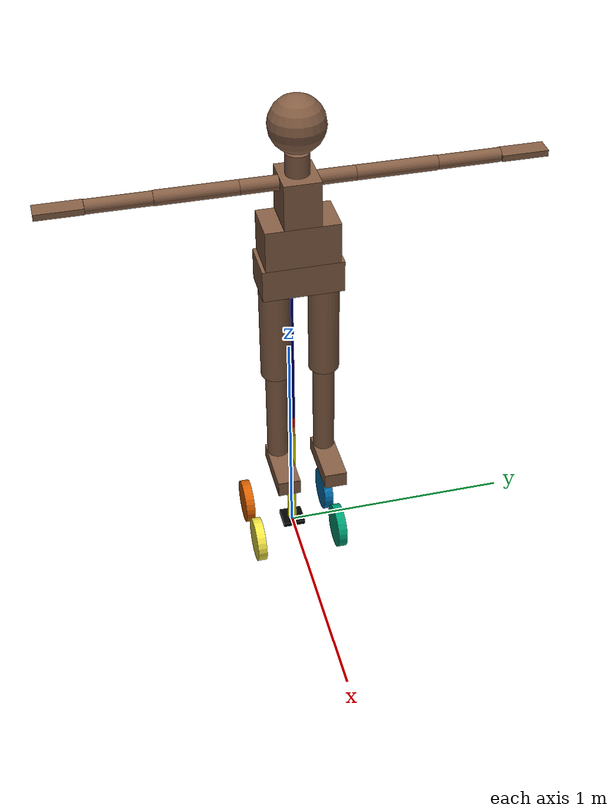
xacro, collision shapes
<?xml version="1.0"?>
<robot xmlns:xacro="http://www.ros.org/wiki/xacro" name="human_support">
    <xacro:arg name="initial_positions_file" default="initial_positions.yaml" />
    <xacro:arg name="namespace" default="humanoid_1" />

    <!-- Import human_support urdf file -->
    <xacro:include filename="$(find humanoid_robot)/model/support/human_support.xacro" />

    <!-- Import control_xacro -->
    <xacro:include filename="human_support.ros2_control.xacro" />
    <xacro:include filename="human_support_wheels.urdf.xacro" />

    <xacro:human_support_ros2_control name="GazeboSimSystem" initial_positions_file="$(arg initial_positions_file)" namespace="$(arg namespace)"/>

</robot>

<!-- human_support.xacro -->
<robot xmlns:xacro="http://www.ros.org/wiki/xacro" name="human_support">

    <xacro:include filename="common_properties.xacro"/>
    <xacro:include filename="arm_3dof.xacro"/>
    <xacro:include filename="$(find humanoid_robot)/humanSubjectWithMesh_simplified.urdf"/>

     <joint name="arm_human_joint" type="fixed">
        <origin xyz="${(arm_base_length)*2} 0.0 ${twist_arm_length}" rpy="0.0 0.0 0.0"/>
        <parent link="link4"/>
        <child link="Pelvis"/>
    </joint>

    <gazebo>
        <plugin filename="gz-sim-pose-publisher-system" name="gz::sim::systems::PosePublisher">
            <publish_link_pose>false</publish_link_pose>
            <publish_collision_pose>false</publish_collision_pose>
            <publish_visual_pose>false</publish_visual_pose>
            <publish_nested_model_pose>true</publish_nested_model_pose>
        </plugin>
    </gazebo>
</robot>

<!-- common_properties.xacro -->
<robot xmlns:xacro="http://www.ros.org/wiki/xacro">

    <material name="blue">
        <color rgba="0.0 0.0 0.5 1.0"/>
    </material>

    <material name="grey">
        <color rgba="0.5 0.5 0.5 1.0"/>
    </material>

    <material name="orange">
        <color rgba="1.0 0.5 0.0 1.0"/>
    </material>

    <material name="yellow">
        <color rgba="1.0 1.0 0.0 1.0"/>
    </material>

    <material name="black">
        <color rgba="0 0 0 1"/>
    </material>

    <material name="red">
        <color rgba="1 0 0 1"/>
    </material>

    <xacro:macro name="box_inertia" params="m l w h xyz rpy">
        <inertial>
            <origin xyz="${xyz}" rpy="${rpy}"/>
            <mass value="${m}"/>
            <inertia ixx="${(m/12) * (h*h+w*w)}" ixy="0.0" ixz="0.0"
                     iyy="${(m/12) * (l*l+h*h)}" iyz="0.0"
                     izz="${(m/12) * (l*l+w*w)}"/>
        </inertial>
    </xacro:macro>

    <xacro:macro name="cylinder_inertia" params="m r h xyz rpy">
        <inertial>
            <origin xyz="${xyz}" rpy="${rpy}"/>
            <mass value="${m}"/>
            <inertia ixx="${(m/12) * (3*r*r + h*h)}" ixy="0.0" ixz="0.0"
                     iyy="${(m/12) * (3*r*r + h*h)}" iyz="0.0"
                     izz="${(m/2) * (r*r)}"/>
        </inertial>
    </xacro:macro>

    <xacro:macro name="sphere_inertia" params="m r xyz rpy">
        <inertial>
            <origin xyz="${xyz}" rpy="${rpy}"/>
            <mass value="${m}"/>
            <inertia ixx="${(2/5) * m * r*r}" ixy="0.0" ixz="0.0"
                     iyy="${(2/5) * m * r*r}" iyz="0.0"
                     izz="${(2/5) * m * r*r}"/>
        </inertial>
    </xacro:macro>

</robot>

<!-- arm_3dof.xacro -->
<robot xmlns:xacro="http://www.ros.org/wiki/xacro">

    <xacro:property name="arm_base_length" value="0.1"/>
    <xacro:property name="arm_base_width" value="0.1"/>
    <xacro:property name="arm_base_height" value="0.02"/>
    <xacro:property name="arm_radius" value="0.02"/>
    <xacro:property name="arm_length" value="0.25"/>

    <!-- length link1 should be at least the length of foot collision box (0.2584 meters) -->
    <xacro:property name="link1_length" value="0.5"/>
    <!-- revolute arm links are small to keep the movement gathered -->
    <xacro:property name="revolute_arm_length" value="0.05"/>
    <!-- twist arm length is the rest of the length to get to 1 meter from end of link 1 -->
    <xacro:property name="twist_arm_length" value="${1-(revolute_arm_length*2)}"/>

    <link name="base_link">
        <visual>
            <geometry>
                <box size="${arm_base_length} ${arm_base_width} ${arm_base_height}"/>
            </geometry>
            <origin xyz="0.0 0.0 ${arm_base_height/2}" rpy="0.0 0.0 0.0"/>
            <material name="black"/>
        </visual>
        <collision>
            <geometry>
                <box size="${arm_base_length} ${arm_base_width} ${arm_base_height}"/>
            </geometry>
            <origin xyz="0.0 0.0 ${arm_base_height/2}" rpy="0.0 0.0 0.0"/>
        </collision>
        <xacro:box_inertia m="0.5" l="${arm_base_length}" w="${arm_base_width}" h="${arm_base_height}"
                           xyz="0.0 0.0 ${arm_base_height/2.0}" rpy="0.0 0.0 0.0" />
    </link>

    <link name="link1">
        <visual>
            <geometry>
                <cylinder radius="${arm_radius}" length="${link1_length}"/>
            </geometry>
            <origin xyz="0.0 0.0 ${link1_length/2}" rpy="0.0 0.0 0.0"/>
            <material name="yellow"/>
        </visual>
        <collision>
            <geometry>
                <cylinder radius="${arm_radius}" length="${link1_length}"/>
            </geometry>
            <origin xyz="0.0 0.0 ${link1_length/2}" rpy="0.0 0.0 0.0"/>
        </collision>
        <xacro:cylinder_inertia m="0.3" r="${arm_radius}" h="${link1_length}"
                                xyz="0.0 0.0 ${link1_length/2}" rpy="0.0 0.0 0.0" />
    </link>

    <link name="link2">
        <visual>
            <geometry>
                <cylinder radius="${arm_radius}" length="${revolute_arm_length}"/>
            </geometry>
            <origin xyz="0.0 0.0 ${revolute_arm_length/2}" rpy="0.0 0.0 0.0"/>
            <material name="orange"/>
        </visual>
        <collision>
            <geometry>
                <cylinder radius="${arm_radius}" length="${revolute_arm_length}"/>
            </geometry>
            <origin xyz="0.0 0.0 ${revolute_arm_length/2}" rpy="0.0 0.0 0.0"/>
        </collision>
        <xacro:cylinder_inertia m="0.3" r="${arm_radius}" h="${revolute_arm_length}"
                                xyz="0.0 0.0 ${revolute_arm_length/2}" rpy="0.0 0.0 0.0" />
    </link>

    <link name="link3">
        <visual>
            <geometry>
                <cylinder radius="${arm_radius}" length="${revolute_arm_length}"/>
            </geometry>
            <origin xyz="0.0 0.0 ${revolute_arm_length/2}" rpy="0.0 0.0 0.0"/>
            <material name="red"/>
        </visual>
        <collision>
            <geometry>
                <cylinder radius="${arm_radius}" length="${revolute_arm_length}"/>
            </geometry>
            <origin xyz="0.0 0.0 ${revolute_arm_length/2}" rpy="0.0 0.0 0.0"/>
        </collision>
        <xacro:cylinder_inertia m="0.3" r="${arm_radius}" h="${revolute_arm_length}"
                                xyz="0.0 0.0 ${revolute_arm_length/2}" rpy="0.0 0.0 0.0" />
    </link>

    <link name="link4">
        <visual>
            <geometry>
                <cylinder radius="${arm_radius}" length="${twist_arm_length}"/>
            </geometry>
            <origin xyz="0.0 0.0 ${twist_arm_length/2}" rpy="0.0 0.0 0.0"/>
            <material name="blue"/>
        </visual>
        <collision>
            <geometry>
                <cylinder radius="${arm_radius}" length="${twist_arm_length}"/>
            </geometry>
            <origin xyz="0.0 0.0 ${twist_arm_length/2}" rpy="0.0 0.0 0.0"/>
        </collision>
        <xacro:cylinder_inertia m="0.3" r="${arm_radius}" h="${twist_arm_length}"
                                xyz="0.0 0.0 ${twist_arm_length/2}" rpy="0.0 0.0 0.0" />
    </link>

    <!-- Fixed joint to slightly raise humanoid before movement -->
    <joint name="base_link1_joint" type="fixed">
        <parent link="base_link"/>
        <child link="link1"/>
        <origin xyz="0 0 ${arm_base_height}" rpy="0 0 0"/>
    </joint>

    <joint name="link1_link2_joint" type="revolute">
        <parent link="link1"/>
        <child link="link2"/>
        <axis xyz="1 0 0"/>
        <limit lower="${-pi/2}" upper="${pi/2}" velocity="100.0" effort="1000.0"/>
        <origin xyz="0 0 ${link1_length}" rpy="0 0 0"/>
    </joint>

    <joint name="link2_link3_joint" type="revolute">
        <parent link="link2"/>
        <child link="link3"/>
        <axis xyz="0 1 0"/>
        <limit lower="${-pi/2}" upper="${pi/2}" velocity="100.0" effort="1000.0"/>
        <origin xyz="0 0 ${revolute_arm_length}" rpy="0 0 0"/>
    </joint>

    <joint name="link3_link4_joint" type="revolute">
        <parent link="link3"/>
        <child link="link4"/>
        <axis xyz="0 0 1"/>
        <limit lower="${-pi/2}" upper="${pi/2}" velocity="100.0" effort="1000.0"/>
        <origin xyz="0 0 ${revolute_arm_length}" rpy="0 0 0"/>
    </joint>

</robot>

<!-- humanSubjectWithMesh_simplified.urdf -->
<robot name="HumanModel">

  <link name="Pelvis">
    <inertial>
      <origin xyz="0.0 0.0 0.0" rpy="0.0 0.0 0.0"/>
      <mass value="0.07098"/>
      <inertia ixx="0.072762100775" ixy="0.0" ixz="0.0" iyy="0.028514890039999997" iyz="0.0" izz="0.080476585735"/>
    </inertial>
    <visual name="Pelvis">
      <geometry>
        <mesh filename="file://$(find humanoid_robot)/meshes/Pelvis.stl" scale="0.58333333 1.03030303 1.03030303"/>
      </geometry>
      <material name="Link">
        <color rgba="0.51 0.36 0.26 1.0"/>
      </material>
      <origin xyz="0.0 0.0 0.0" rpy="0.0 0.0 0.0"/>
    </visual>
    <visual name="Pelvis_RightRecAbd">
      <geometry>
        <mesh filename="file://$(find humanoid_robot)/meshes/Pelvis_RightRecAbd.stl" scale="0.58333333 1.03030303 1.03030303"/>
      </geometry>
      <material name="muscle">
        <color rgba="0.51 0.36 0.26 1.0"/>
      </material>
      <origin xyz="0.0 0.0 0.0" rpy="0.0 0.0 0.0"/>
    </visual>
    <visual name="Pelvis_RightErcSpin">
      <geometry>
        <mesh filename="file://$(find humanoid_robot)/meshes/Pelvis_RightErcSpin.stl" scale="0.58333333 1.03030303 1.03030303"/>
      </geometry>
      <material name="muscle">
        <color rgba="0.51 0.36 0.26 1.0"/>
      </material>
      <origin xyz="0.0 0.0 0.0" rpy="0.0 0.0 0.0"/>
    </visual>
    <visual name="Pelvis_LeftRecAbd">
      <geometry>
        <mesh filename="file://$(find humanoid_robot)/meshes/Pelvis_LeftRecAbd.stl" scale="0.58333333 1.03030303 1.03030303"/>
      </geometry>
      <material name="muscle">
        <color rgba="0.51 0.36 0.26 1.0"/>
      </material>
      <origin xyz="0.0 0.0 0.0" rpy="0.0 0.0 0.0"/>
    </visual>
    <visual name="Pelvis_LeftErcSpin">
      <geometry>
        <mesh filename="file://$(find humanoid_robot)/meshes/Pelvis_LeftErcSpin.stl" scale="0.58333333 1.03030303 1.03030303"/>
      </geometry>
      <material name="muscle">
        <color rgba="0.51 0.36 0.26 1.0"/>
      </material>
      <origin xyz="0.0 0.0 0.0" rpy="0.0 0.0 0.0"/>
    </visual>
    <collision>
      <geometry>
        <box size="0.175  0.3247 0.1326"/>
      </geometry>
      <origin xyz="0.0 0.0 0.0" rpy="0.0 0.0 0.0"/>
    </collision>
  </link>
  <link name="LowerTrunk_f1">
    <inertial>
      <origin xyz="0.0 0.0 0.0" rpy="0.0 0.0 0.0"/>
      <mass value="0.01"/>
      <inertia ixx="0.01" ixy="0.0" ixz="0.0" iyy="0.01" iyz="0.0" izz="0.01"/>
    </inertial>
  </link>
  <link name="LowerTrunk">
    <inertial>
      <origin xyz="0.0 0.0 0.085" rpy="0.0 0.0 0.0"/>
      <mass value="0.09294"/>
      <inertia ixx="0.09014997218" ixy="0.0" ixz="0.0" iyy="0.04610211250000001" iyz="0.0" izz="0.09148598468"/>
    </inertial>
    <visual name="LowerTrunk">
      <geometry>
        <mesh filename="file://$(find humanoid_robot)/meshes/LowerTrunk.stl" scale="0.58333333 1.03030303 1.03030303"/>
      </geometry>
      <material name="Link">
        <color rgba="0.51 0.36 0.26 1.0"/>
      </material>
      <origin xyz="0.0 0.0 0.085" rpy="0.0 0.0 0.0"/>
    </visual>
    <visual name="LowerTrunk_RightRecAbd">
      <geometry>
        <mesh filename="file://$(find humanoid_robot)/meshes/LowerTrunk_RightRecAbd.stl" scale="0.58333333 1.03030303 1.03030303"/>
      </geometry>
      <material name="muscle">
        <color rgba="0.51 0.36 0.26 1.0"/>
      </material>
      <origin xyz="0.0 0.0 0.085" rpy="0.0 0.0 0.0"/>
    </visual>
    <visual name="LowerTrunk_RightErcSpin">
      <geometry>
        <mesh filename="file://$(find humanoid_robot)/meshes/LowerTrunk_RightErcSpin.stl" scale="0.58333333 1.03030303 1.03030303"/>
      </geometry>
      <material name="muscle">
        <color rgba="0.51 0.36 0.26 1.0"/>
      </material>
      <origin xyz="0.0 0.0 0.085" rpy="0.0 0.0 0.0"/>
    </visual>
    <visual name="LowerTrunk_LefttRecAbd">
      <geometry>
        <mesh filename="file://$(find humanoid_robot)/meshes/LowerTrunk_LefttRecAbd.stl" scale="0.58333333 1.03030303 1.03030303"/>
      </geometry>
      <material name="muscle">
        <color rgba="0.51 0.36 0.26 1.0"/>
      </material>
      <origin xyz="0.0 0.0 0.085" rpy="0.0 0.0 0.0"/>
    </visual>
    <visual name="LowerTrunk_LeftErcSpin">
      <geometry>
        <mesh filename="file://$(find humanoid_robot)/meshes/LowerTrunk_LeftErcSpin.stl" scale="0.58333333 1.03030303 1.03030303"/>
      </geometry>
      <material name="muscle">
        <color rgba="0.51 0.36 0.26 1.0"/>
      </material>
      <origin xyz="0.0 0.0 0.085" rpy="0.0 0.0 0.0"/>
    </visual>
    <collision>
      <geometry>
        <box size="0.175  0.2958 0.17  "/>
      </geometry>
      <origin xyz="0.0 0.0 0.085" rpy="0.0 0.0 0.0"/>
    </collision>
  </link>
  <link name="UpperTrunk_f1">
    <inertial>
      <origin xyz="0.0 0.0 0.0" rpy="0.0 0.0 0.0"/>
      <mass value="0.01"/>
      <inertia ixx="0.01" ixy="0.0" ixz="0.0" iyy="0.01" iyz="0.0" izz="0.01"/>
    </inertial>
  </link>
  <link name="UpperTrunk_f2">
    <inertial>
      <origin xyz="0.0 0.0 0.0" rpy="0.0 0.0 0.0"/>
      <mass value="0.01"/>
      <inertia ixx="0.01" ixy="0.0" ixz="0.0" iyy="0.01" iyz="0.0" izz="0.01"/>
    </inertial>
  </link>
  <link name="UpperTrunk">
    <inertial>
      <origin xyz="0.0 0.0 0.0935" rpy="0.0 0.0 0.0"/>
      <mass value="0.03138"/>
      <inertia ixx="0.014777222337222225" ixy="0.0" ixz="0.0" iyy="0.017152831" iyz="0.0" izz="0.013641266337222223"/>
    </inertial>
    <visual name="UpperTrunk">
      <geometry>
        <mesh filename="file://$(find humanoid_robot)/meshes/UpperTrunk.stl" scale="0.58333333 1.03030303 1.03030303"/>
      </geometry>
      <material name="Link">
        <color rgba="0.51 0.36 0.26 1.0"/>
      </material>
      <origin xyz="0.0 0.0 0.0935" rpy="0.0 0.0 0.0"/>
    </visual>
    <visual name="UpperTrunk_RightRecAbd">
      <geometry>
        <mesh filename="file://$(find humanoid_robot)/meshes/UpperTrunk_RightRecAbd.stl" scale="0.58333333 1.03030303 1.03030303"/>
      </geometry>
      <material name="muscle">
        <color rgba="0.51 0.36 0.26 1.0"/>
      </material>
      <origin xyz="0.0 0.0 0.0935" rpy="0.0 0.0 0.0"/>
    </visual>
    <visual name="UpperTrunk_RightErcSpin">
      <geometry>
        <mesh filename="file://$(find humanoid_robot)/meshes/UpperTrunk_RightErcSpin.stl" scale="0.58333333 1.03030303 1.03030303"/>
      </geometry>
      <material name="muscle">
        <color rgba="0.51 0.36 0.26 1.0"/>
      </material>
      <origin xyz="0.0 0.0 0.0935" rpy="0.0 0.0 0.0"/>
    </visual>
    <visual name="UpperTrunk_LeftRecAbd">
      <geometry>
        <mesh filename="file://$(find humanoid_robot)/meshes/UpperTrunk_LeftRecAbd.stl" scale="0.58333333 1.03030303 1.03030303"/>
      </geometry>
      <material name="muscle">
        <color rgba="0.51 0.36 0.26 1.0"/>
      </material>
      <origin xyz="0.0 0.0 0.0935" rpy="0.0 0.0 0.0"/>
    </visual>
    <visual name="UpperTrunk_LeftErcSpin">
      <geometry>
        <mesh filename="file://$(find humanoid_robot)/meshes/UpperTrunk_LeftErcSpin.stl" scale="0.58333333 1.03030303 1.03030303"/>
      </geometry>
      <material name="muscle">
        <color rgba="0.51 0.36 0.26 1.0"/>
      </material>
      <origin xyz="0.0 0.0 0.0935" rpy="0.0 0.0 0.0"/>
    </visual>
    <collision>
      <geometry>
        <box size="0.175      0.14676667 0.187     "/>
      </geometry>
      <origin xyz="0.0 0.0 0.0935" rpy="0.0 0.0 0.0"/>
    </collision>
  </link>
  <link name="RightShoulder">
    <inertial>
      <origin xyz="0.0 -0.07338333333333334 0.0" rpy="1.5708 0.0 0.0"/>
      <mass value="0.03138"/>
      <inertia ixx="0.01" ixy="0.0" ixz="0.0" iyy="0.01" iyz="0.0" izz="0.01"/>
    </inertial>
    <visual name="RightShoulder">
      <geometry>
        <mesh filename="file://$(find humanoid_robot)/meshes/RightShoulder.stl" scale="0.64444444 0.64444444 1.03030303"/>
      </geometry>
      <material name="Link">
        <color rgba="0.51 0.36 0.26 1.0"/>
      </material>
      <origin xyz="0.0 -0.07338333333333334 0.0" rpy="1.5708 0.0 0.0"/>
    </visual>
    <collision>
      <geometry>
        <cylinder radius="0.029" length="0.14676666666666668"/>
      </geometry>
      <origin xyz="0.0 -0.07338333333333334 0.0" rpy="1.5708 0.0 0.0"/>
    </collision>
  </link>
  <link name="LeftShoulder">
    <inertial>
      <origin xyz="0.0 0.07338333333333334 0.0" rpy="1.5708 0.0 0.0"/>
      <mass value="0.03138"/>
      <inertia ixx="0.01" ixy="0.0" ixz="0.0" iyy="0.01" iyz="0.0" izz="0.01"/>
    </inertial>
    <visual name="LeftShoulder">
      <geometry>
        <mesh filename="file://$(find humanoid_robot)/meshes/LeftShoulder.stl" scale="0.64444444 0.64444444 1.03030303"/>
      </geometry>
      <material name="Link">
        <color rgba="0.51 0.36 0.26 1.0"/>
      </material>
      <origin xyz="0.0 0.07338333333333334 0.0" rpy="1.5708 0.0 0.0"/>
    </visual>
    <collision>
      <geometry>
        <cylinder radius="0.029" length="0.14676666666666668"/>
      </geometry>
      <origin xyz="0.0 0.07338333333333334 0.0" rpy="1.5708 0.0 0.0"/>
    </collision>
  </link>
  <link name="Neck_f1">
    <inertial>
      <origin xyz="0.0 0.0 0.0" rpy="0.0 0.0 0.0"/>
      <mass value="0.01"/>
      <inertia ixx="0.01" ixy="0.0" ixz="0.0" iyy="0.01" iyz="0.0" izz="0.01"/>
    </inertial>
  </link>
  <link name="Neck_f2">
    <inertial>
      <origin xyz="0.0 0.0 0.0" rpy="0.0 0.0 0.0"/>
      <mass value="0.01"/>
      <inertia ixx="0.01" ixy="0.0" ixz="0.0" iyy="0.01" iyz="0.0" izz="0.01"/>
    </inertial>
  </link>
  <link name="Neck">
    <inertial>
      <origin xyz="0.0 0.0 0.044199999999999996" rpy="0.0 0.0 0.0"/>
      <mass value="0.011640000000000001"/>
      <inertia ixx="0.01" ixy="0.0" ixz="0.0" iyy="0.01" iyz="0.0" izz="0.01"/>
    </inertial>
    <visual name="Neck">
      <geometry>
        <mesh filename="file://$(find humanoid_robot)/meshes/Neck.stl" scale="0.73076923 0.73076923 1.03030303"/>
      </geometry>
      <material name="Link">
        <color rgba="0.51 0.36 0.26 1.0"/>
      </material>
      <origin xyz="0.0 0.0 0.044199999999999996" rpy="0.0 0.0 0.0"/>
    </visual>
    <collision>
      <geometry>
        <cylinder radius="0.0475" length="0.08839999999999999"/>
      </geometry>
      <origin xyz="0.0 0.0 0.044199999999999996" rpy="0.0 0.0 0.0"/>
    </collision>
  </link>
  <link name="Head_f1">
    <inertial>
      <origin xyz="0.0 0.0 0.0" rpy="0.0 0.0 0.0"/>
      <mass value="0.01"/>
      <inertia ixx="0.01" ixy="0.0" ixz="0.0" iyy="0.01" iyz="0.0" izz="0.01"/>
    </inertial>
  </link>
  <link name="Head">
    <inertial>
      <origin xyz="0.0 0.0 0.1105" rpy="0.0 0.0 0.0"/>
      <mass value="0.02922"/>
      <inertia ixx="0.014271340200000001" ixy="0.0" ixz="0.0" iyy="0.014271340200000001" iyz="0.0" izz="0.014271340200000001"/>
    </inertial>
    <visual name="Head">
      <geometry>
        <mesh filename="file://$(find humanoid_robot)/meshes/Head.stl" scale="1.03030303 1.03030303 1.03030303"/>
      </geometry>
      <material name="Link">
        <color rgba="0.51 0.36 0.26 1.0"/>
      </material>
      <origin xyz="0.0 0.0 0.1105" rpy="0.0 0.0 0.0"/>
    </visual>
    <collision>
      <geometry>
        <sphere radius="0.1105"/>
      </geometry>
      <origin xyz="0.0 0.0 0.1105" rpy="0.0 0.0 0.0"/>
    </collision>
  </link>
  <gazebo reference="Head">
      <visual>
          <material>
            <color rgba="0.51 0.36 0.26 1.0"/>
          </material>
      </visual>
  </gazebo>
  <link name="RightShoulder_f1">
    <inertial>
      <origin xyz="0.0 0.0 0.0" rpy="0.0 0.0 0.0"/>
      <mass value="0.01"/>
      <inertia ixx="0.01" ixy="0.0" ixz="0.0" iyy="0.01" iyz="0.0" izz="0.01"/>
    </inertial>
  </link>
  <link name="RightShoulder_f2">
    <inertial>
      <origin xyz="0.0 0.0 0.0" rpy="0.0 0.0 0.0"/>
      <mass value="0.01"/>
      <inertia ixx="0.01" ixy="0.0" ixz="0.0" iyy="0.01" iyz="0.0" izz="0.01"/>
    </inertial>
  </link>
  <link name="RightUpperArm">
    <inertial>
      <origin xyz="0.0 -0.1581 0.0" rpy="1.5708 0.0 0.0"/>
      <mass value="0.01578"/>
      <inertia ixx="0.013479465359999998" ixy="0.0" ixz="0.0" iyy="0.013479465359999998" iyz="0.0" izz="0.01"/>
    </inertial>
    <visual name="RightUpperArm">
      <geometry>
        <mesh filename="file://$(find humanoid_robot)/meshes/RightUpperArm.stl" scale="0.64444444 0.64444444 1.03030303"/>
      </geometry>
      <material name="Link">
        <color rgba="0.51 0.36 0.26 1.0"/>
      </material>
      <origin xyz="0.0 -0.1581 0.0" rpy="1.5708 0.0 0.0"/>
    </visual>
    <visual name="RightTricBrac">
      <geometry>
        <mesh filename="file://$(find humanoid_robot)/meshes/RightTricBrac.stl" scale="0.64444444 0.64444444 1.03030303"/>
      </geometry>
      <material name="muscle">
        <color rgba="0.51 0.36 0.26 1.0"/>
      </material>
      <origin xyz="0.0 -0.1581 0.0" rpy="1.5708 0.0 0.0"/>
    </visual>
    <visual name="RightBicBrac">
      <geometry>
        <mesh filename="file://$(find humanoid_robot)/meshes/RightBicBrac.stl" scale="0.64444444 0.64444444 1.03030303"/>
      </geometry>
      <material name="muscle">
        <color rgba="0.51 0.36 0.26 1.0"/>
      </material>
      <origin xyz="0.0 -0.1581 0.0" rpy="1.5708 0.0 0.0"/>
    </visual>
    <collision>
      <geometry>
        <cylinder radius="0.029" length="0.3162"/>
      </geometry>
      <origin xyz="0.0 -0.1581 0.0" rpy="1.5708 0.0 0.0"/>
    </collision>
  </link>
  <link name="RightForeArm_f1">
    <inertial>
      <origin xyz="0.0 0.0 0.0" rpy="0.0 0.0 0.0"/>
      <mass value="0.01"/>
      <inertia ixx="0.01" ixy="0.0" ixz="0.0" iyy="0.01" iyz="0.0" izz="0.01"/>
    </inertial>
  </link>
  <link name="RightForeArm">
    <inertial>
      <origin xyz="0.0 -0.12409999999999999 0.0" rpy="1.5708 0.0 0.0"/>
      <mass value="0.008999999999999999"/>
      <inertia ixx="0.01" ixy="0.0" ixz="0.0" iyy="0.01" iyz="0.0" izz="0.01"/>
    </inertial>
    <visual name="RightForeArm">
      <geometry>
        <mesh filename="file://$(find humanoid_robot)/meshes/RightForeArm.stl" scale="0.61111111 0.61111111 1.03030303"/>
      </geometry>
      <material name="Link">
        <color rgba="0.51 0.36 0.26 1.0"/>
      </material>
      <origin xyz="0.0 -0.12409999999999999 0.0" rpy="1.5708 0.0 0.0"/>
    </visual>
    <visual name="RightFlexCarp">
      <geometry>
        <mesh filename="file://$(find humanoid_robot)/meshes/RightFlexCarp.stl" scale="0.61111111 0.61111111 1.03030303"/>
      </geometry>
      <material name="muscle">
        <color rgba="0.51 0.36 0.26 1.0"/>
      </material>
      <origin xyz="0.0 -0.12409999999999999 0.0" rpy="1.5708 0.0 0.0"/>
    </visual>
    <visual name="RightExtCarp">
      <geometry>
        <mesh filename="file://$(find humanoid_robot)/meshes/RightExtCarp.stl" scale="0.61111111 0.61111111 1.03030303"/>
      </geometry>
      <material name="muscle">
        <color rgba="0.51 0.36 0.26 1.0"/>
      </material>
      <origin xyz="0.0 -0.12409999999999999 0.0" rpy="1.5708 0.0 0.0"/>
    </visual>
    <collision>
      <geometry>
        <cylinder radius="0.0275" length="0.24819999999999998"/>
      </geometry>
      <origin xyz="0.0 -0.12409999999999999 0.0" rpy="1.5708 0.0 0.0"/>
    </collision>
  </link>
  <link name="RightHand_f1">
    <inertial>
      <origin xyz="0.0 0.0 0.0" rpy="0.0 0.0 0.0"/>
      <mass value="0.01"/>
      <inertia ixx="0.01" ixy="0.0" ixz="0.0" iyy="0.01" iyz="0.0" izz="0.01"/>
    </inertial>
  </link>
  <link name="RightHand">
    <inertial>
      <origin xyz="0.0 -0.09179999999999999 0.0" rpy="0.0 0.0 0.0"/>
      <mass value="0.00354"/>
      <inertia ixx="0.01" ixy="0.0" ixz="0.0" iyy="0.01" iyz="0.0" izz="0.01"/>
    </inertial>
    <visual name="RightHand">
      <geometry>
        <mesh filename="file://$(find humanoid_robot)/meshes/RightHand.stl" scale="0.9        1.03030303 0.55555556"/>
      </geometry>
      <material name="Link">
        <color rgba="0.51 0.36 0.26 1.0"/>
      </material>
      <origin xyz="0.0 -0.09179999999999999 0.0" rpy="0.0 0.0 0.0"/>
    </visual>
    <collision>
      <geometry>
        <box size="0.072  0.1836 0.025 "/>
      </geometry>
      <origin xyz="0.0 -0.09179999999999999 0.0" rpy="0.0 0.0 0.0"/>
    </collision>
  </link>
  <link name="LeftShoulder_f1">
    <inertial>
      <origin xyz="0.0 0.0 0.0" rpy="0.0 0.0 0.0"/>
      <mass value="0.01"/>
      <inertia ixx="0.01" ixy="0.0" ixz="0.0" iyy="0.01" iyz="0.0" izz="0.01"/>
    </inertial>
  </link>
  <link name="LeftShoulder_f2">
    <inertial>
      <origin xyz="0.0 0.0 0.0" rpy="0.0 0.0 0.0"/>
      <mass value="0.01"/>
      <inertia ixx="0.01" ixy="0.0" ixz="0.0" iyy="0.01" iyz="0.0" izz="0.01"/>
    </inertial>
  </link>
  <link name="LeftUpperArm">
    <inertial>
      <origin xyz="0.0 0.1581 0.0" rpy="1.5708 0.0 0.0"/>
      <mass value="0.01578"/>
      <inertia ixx="0.013479465359999998" ixy="0.0" ixz="0.0" iyy="0.013479465359999998" iyz="0.0" izz="0.01"/>
    </inertial>
    <visual name="LeftUpperArm">
      <geometry>
        <mesh filename="file://$(find humanoid_robot)/meshes/LeftUpperArm.stl" scale="0.64444444 0.64444444 1.03030303"/>
      </geometry>
      <material name="Link">
        <color rgba="0.51 0.36 0.26 1.0"/>
      </material>
      <origin xyz="0.0 0.1581 0.0" rpy="1.5708 0.0 0.0"/>
    </visual>
    <visual name="LeftTricBrac">
      <geometry>
        <mesh filename="file://$(find humanoid_robot)/meshes/LeftTricBrac.stl" scale="0.64444444 0.64444444 1.03030303"/>
      </geometry>
      <material name="muscle">
        <color rgba="0.51 0.36 0.26 1.0"/>
      </material>
      <origin xyz="0.0 0.1581 0.0" rpy="1.5708 0.0 0.0"/>
    </visual>
    <visual name="LeftBicBrac">
      <geometry>
        <mesh filename="file://$(find humanoid_robot)/meshes/LeftBicBrac.stl" scale="0.64444444 0.64444444 1.03030303"/>
      </geometry>
      <material name="muscle">
        <color rgba="0.51 0.36 0.26 1.0"/>
      </material>
      <origin xyz="0.0 0.1581 0.0" rpy="1.5708 0.0 0.0"/>
    </visual>
    <collision>
      <geometry>
        <cylinder radius="0.029" length="0.3162"/>
      </geometry>
      <origin xyz="0.0 0.1581 0.0" rpy="1.5708 0.0 0.0"/>
    </collision>
  </link>
  <link name="LeftForeArm_f1">
    <inertial>
      <origin xyz="0.0 0.0 0.0" rpy="0.0 0.0 0.0"/>
      <mass value="0.01"/>
      <inertia ixx="0.01" ixy="0.0" ixz="0.0" iyy="0.01" iyz="0.0" izz="0.01"/>
    </inertial>
  </link>
  <link name="LeftForeArm">
    <inertial>
      <origin xyz="0.0 0.12409999999999999 0.0" rpy="1.5708 0.0 0.0"/>
      <mass value="0.008999999999999999"/>
      <inertia ixx="0.01" ixy="0.0" ixz="0.0" iyy="0.01" iyz="0.0" izz="0.01"/>
    </inertial>
    <visual name="LeftForeArm">
      <geometry>
        <mesh filename="file://$(find humanoid_robot)/meshes/LeftForeArm.stl" scale="0.61111111 0.61111111 1.03030303"/>
      </geometry>
      <material name="Link">
        <color rgba="0.51 0.36 0.26 1.0"/>
      </material>
      <origin xyz="0.0 0.12409999999999999 0.0" rpy="1.5708 0.0 0.0"/>
    </visual>
    <visual name="LeftFlexCarp">
      <geometry>
        <mesh filename="file://$(find humanoid_robot)/meshes/LeftFlexCarp.stl" scale="0.61111111 0.61111111 1.03030303"/>
      </geometry>
      <material name="muscle">
        <color rgba="0.51 0.36 0.26 1.0"/>
      </material>
      <origin xyz="0.0 0.12409999999999999 0.0" rpy="1.5708 0.0 0.0"/>
    </visual>
    <visual name="LeftExtCarp">
      <geometry>
        <mesh filename="file://$(find humanoid_robot)/meshes/LeftExtCarp.stl" scale="0.61111111 0.61111111 1.03030303"/>
      </geometry>
      <material name="muscle">
        <color rgba="0.51 0.36 0.26 1.0"/>
      </material>
      <origin xyz="0.0 0.12409999999999999 0.0" rpy="1.5708 0.0 0.0"/>
    </visual>
    <collision>
      <geometry>
        <cylinder radius="0.0275" length="0.24819999999999998"/>
      </geometry>
      <origin xyz="0.0 0.12409999999999999 0.0" rpy="1.5708 0.0 0.0"/>
    </collision>
  </link>
  <link name="LeftHand_f1">
    <inertial>
      <origin xyz="0.0 0.0 0.0" rpy="0.0 0.0 0.0"/>
      <mass value="0.01"/>
      <inertia ixx="0.01" ixy="0.0" ixz="0.0" iyy="0.01" iyz="0.0" izz="0.01"/>
    </inertial>
  </link>
  <link name="LeftHand">
    <inertial>
      <origin xyz="0.0 0.09179999999999999 0.0" rpy="0.0 0.0 0.0"/>
      <mass value="0.00354"/>
      <inertia ixx="0.01" ixy="0.0" ixz="0.0" iyy="0.01" iyz="0.0" izz="0.01"/>
    </inertial>
    <visual name="LeftHand">
      <geometry>
        <mesh filename="file://$(find humanoid_robot)/meshes/LeftHand.stl" scale="0.9        1.03030303 0.55555556"/>
      </geometry>
      <material name="Link">
        <color rgba="0.51 0.36 0.26 1.0"/>
      </material>
      <origin xyz="0.0 0.09179999999999999 0.0" rpy="0.0 0.0 0.0"/>
    </visual>
    <collision>
      <geometry>
        <box size="0.072  0.1836 0.025 "/>
      </geometry>
      <origin xyz="0.0 0.09179999999999999 0.0" rpy="0.0 0.0 0.0"/>
    </collision>
  </link>
  <link name="RightUpperLeg_f1">
    <inertial>
      <origin xyz="0.0 0.0 0.0" rpy="0.0 0.0 0.0"/>
      <mass value="0.01"/>
      <inertia ixx="0.01" ixy="0.0" ixz="0.0" iyy="0.01" iyz="0.0" izz="0.01"/>
    </inertial>
  </link>
  <link name="RightUpperLeg_f2">
    <inertial>
      <origin xyz="0.0 0.0 0.0" rpy="0.0 0.0 0.0"/>
      <mass value="0.01"/>
      <inertia ixx="0.01" ixy="0.0" ixz="0.0" iyy="0.01" iyz="0.0" izz="0.01"/>
    </inertial>
  </link>
  <link name="RightUpperLeg">
    <inertial>
      <origin xyz="0.0 0.0 -0.20825" rpy="0.0 0.0 0.0"/>
      <mass value="0.08682"/>
      <inertia ixx="0.1339856885" ixy="0.0" ixz="0.0" iyy="0.1339856885" iyz="0.0" izz="0.01695703125"/>
    </inertial>
    <visual name="RightUpperLeg">
      <geometry>
        <mesh filename="file://$(find humanoid_robot)/meshes/RightUpperLeg.stl" scale="0.83333333 0.83333333 1.03030303"/>
      </geometry>
      <material name="Link">
        <color rgba="0.51 0.36 0.26 1.0"/>
      </material>
      <origin xyz="0.0 0.0 -0.20825" rpy="0.0 0.0 0.0"/>
    </visual>
    <visual name="RightRecFem">
      <geometry>
        <mesh filename="file://$(find humanoid_robot)/meshes/RightRecFem.stl" scale="0.83333333 0.83333333 1.03030303"/>
      </geometry>
      <material name="muscle">
        <color rgba="0.51 0.36 0.26 1.0"/>
      </material>
      <origin xyz="0.0 0.0 -0.20825" rpy="0.0 0.0 0.0"/>
    </visual>
    <visual name="RightBicFem">
      <geometry>
        <mesh filename="file://$(find humanoid_robot)/meshes/RightBicFem.stl" scale="0.83333333 0.83333333 1.03030303"/>
      </geometry>
      <material name="muscle">
        <color rgba="0.51 0.36 0.26 1.0"/>
      </material>
      <origin xyz="0.0 0.0 -0.20825" rpy="0.0 0.0 0.0"/>
    </visual>
    <collision>
      <geometry>
        <cylinder radius="0.0625" length="0.4165"/>
      </geometry>
      <origin xyz="0.0 0.0 -0.20825" rpy="0.0 0.0 0.0"/>
    </collision>
  </link>
  <link name="RightLowerLeg_f1">
    <inertial>
      <origin xyz="0.0 0.0 0.0" rpy="0.0 0.0 0.0"/>
      <mass value="0.01"/>
      <inertia ixx="0.01" ixy="0.0" ixz="0.0" iyy="0.01" iyz="0.0" izz="0.01"/>
    </inertial>
  </link>
  <link name="RightLowerLeg">
    <inertial>
      <origin xyz="0.0 0.0 -0.20909999999999998" rpy="0.0 0.0 0.0"/>
      <mass value="0.02742"/>
      <inertia ixx="0.041350785839999994" ixy="0.0" ixz="0.0" iyy="0.041350785839999994" iyz="0.0" izz="0.01"/>
    </inertial>
    <visual name="RightLowerLeg">
      <geometry>
        <mesh filename="file://$(find humanoid_robot)/meshes/RightLowerLeg.stl" scale="0.7826087  0.7826087  1.03030303"/>
      </geometry>
      <material name="Link">
        <color rgba="0.51 0.36 0.26 1.0"/>
      </material>
      <origin xyz="0.0 0.0 -0.20909999999999998" rpy="0.0 0.0 0.0"/>
    </visual>
    <visual name="RightTibAnt">
      <geometry>
        <mesh filename="file://$(find humanoid_robot)/meshes/RightTibAnt.stl" scale="0.7826087  0.7826087  1.03030303"/>
      </geometry>
      <material name="muscle">
        <color rgba="0.51 0.36 0.26 1.0"/>
      </material>
      <origin xyz="0.0 0.0 -0.20909999999999998" rpy="0.0 0.0 0.0"/>
    </visual>
    <visual name="RightGasMed">
      <geometry>
        <mesh filename="file://$(find humanoid_robot)/meshes/RightGasMed.stl" scale="0.7826087  0.7826087  1.03030303"/>
      </geometry>
      <material name="muscle">
        <color rgba="0.51 0.36 0.26 1.0"/>
      </material>
      <origin xyz="0.0 0.0 -0.20909999999999998" rpy="0.0 0.0 0.0"/>
    </visual>
    <visual name="RightGasLat">
      <geometry>
        <mesh filename="file://$(find humanoid_robot)/meshes/RightGasLat.stl" scale="0.7826087  0.7826087  1.03030303"/>
      </geometry>
      <material name="muscle">
        <color rgba="0.51 0.36 0.26 1.0"/>
      </material>
      <origin xyz="0.0 0.0 -0.20909999999999998" rpy="0.0 0.0 0.0"/>
    </visual>
    <collision>
      <geometry>
        <cylinder radius="0.045" length="0.41819999999999996"/>
      </geometry>
      <origin xyz="0.0 0.0 -0.20909999999999998" rpy="0.0 0.0 0.0"/>
    </collision>
  </link>
  <link name="RightFoot_f1">
    <inertial>
      <origin xyz="0.0 0.0 0.0" rpy="0.0 0.0 0.0"/>
      <mass value="0.01"/>
      <inertia ixx="0.01" ixy="0.0" ixz="0.0" iyy="0.01" iyz="0.0" izz="0.01"/>
    </inertial>
  </link>
  <link name="RightFoot_f2">
    <inertial>
      <origin xyz="0.0 0.0 0.0" rpy="0.0 0.0 0.0"/>
      <mass value="0.01"/>
      <inertia ixx="0.01" ixy="0.0" ixz="0.0" iyy="0.01" iyz="0.0" izz="0.01"/>
    </inertial>
  </link>
  <link name="RightFoot">
    <inertial>
      <origin xyz="0.08419999999999998 0.0 -0.03315" rpy="0.0 0.0 0.0"/>
      <mass value="0.0079002"/>
      <inertia ixx="0.01" ixy="0.0" ixz="0.0" iyy="0.01" iyz="0.0" izz="0.01"/>
    </inertial>
    <visual name="RightFoot">
      <geometry>
        <mesh filename="file://$(find humanoid_robot)/meshes/RightFoot.stl" scale="1.03030303 1.03030303 1.03030303"/>
      </geometry>
      <material name="Link">
        <color rgba="0.51 0.36 0.26 1.0"/>
      </material>
      <origin xyz="0.08419999999999998 0.0 -0.03315" rpy="0.0 0.0 0.0"/>
    </visual>
    <collision>
      <geometry>
        <box size="0.2584 0.0935 0.0663"/>
      </geometry>
      <origin xyz="0.08419999999999998 0.0 -0.03315" rpy="0.0 0.0 0.0"/>
    </collision>
  </link>
  <link name="RightToe">
    <inertial>
      <origin xyz="0.0 0.0 0.0" rpy="0.0 0.0 0.0"/>
      <mass value="0.0000798"/>
      <inertia ixx="0.01" ixy="0.0" ixz="0.0" iyy="0.01" iyz="0.0" izz="0.01"/>
    </inertial>
    <visual name="RightToe">
      <geometry>
        <mesh filename="file://$(find humanoid_robot)/meshes/RightToe.stl" scale="1.03030303 1.03030303 1.03030303"/>
      </geometry>
      <material name="Link">
        <color rgba="0.51 0.36 0.26 1.0"/>
      </material>
      <origin xyz="0.0 0.0 0.0" rpy="0.0 0.0 0.0"/>
    </visual>
    <collision>
      <geometry>
        <box size="0.002584 0.0935   0.0663  "/>
      </geometry>
      <origin xyz="0.0 0.0 0.0" rpy="0.0 0.0 0.0"/>
    </collision>
  </link>
  <link name="LeftUpperLeg_f1">
    <inertial>
      <origin xyz="0.0 0.0 0.0" rpy="0.0 0.0 0.0"/>
      <mass value="0.01"/>
      <inertia ixx="0.01" ixy="0.0" ixz="0.0" iyy="0.01" iyz="0.0" izz="0.01"/>
    </inertial>
  </link>
  <link name="LeftUpperLeg_f2">
    <inertial>
      <origin xyz="0.0 0.0 0.0" rpy="0.0 0.0 0.0"/>
      <mass value="0.01"/>
      <inertia ixx="0.01" ixy="0.0" ixz="0.0" iyy="0.01" iyz="0.0" izz="0.01"/>
    </inertial>
  </link>
  <link name="LeftUpperLeg">
    <inertial>
      <origin xyz="0.0 0.0 -0.20825" rpy="0.0 0.0 0.0"/>
      <mass value="0.08682"/>
      <inertia ixx="0.1339856885" ixy="0.0" ixz="0.0" iyy="0.1339856885" iyz="0.0" izz="0.01695703125"/>
    </inertial>
    <visual name="LeftUpperLeg">
      <geometry>
        <mesh filename="file://$(find humanoid_robot)/meshes/LeftUpperLeg.stl" scale="0.83333333 0.83333333 1.03030303"/>
      </geometry>
      <material name="Link">
        <color rgba="0.51 0.36 0.26 1.0"/>
      </material>
      <origin xyz="0.0 0.0 -0.20825" rpy="0.0 0.0 0.0"/>
    </visual>
    <visual name="LeftRecFem">
      <geometry>
        <mesh filename="file://$(find humanoid_robot)/meshes/LeftRecFem.stl" scale="0.83333333 0.83333333 1.03030303"/>
      </geometry>
      <material name="muscle">
        <color rgba="0.51 0.36 0.26 1.0"/>
      </material>
      <origin xyz="0.0 0.0 -0.20825" rpy="0.0 0.0 0.0"/>
    </visual>
    <visual name="LeftBicFem">
      <geometry>
        <mesh filename="file://$(find humanoid_robot)/meshes/LeftBicFem.stl" scale="0.83333333 0.83333333 1.03030303"/>
      </geometry>
      <material name="muscle">
        <color rgba="0.51 0.36 0.26 1.0"/>
      </material>
      <origin xyz="0.0 0.0 -0.20825" rpy="0.0 0.0 0.0"/>
    </visual>
    <collision>
      <geometry>
        <cylinder radius="0.0625" length="0.4165"/>
      </geometry>
      <origin xyz="0.0 0.0 -0.20825" rpy="0.0 0.0 0.0"/>
    </collision>
  </link>
  <link name="LeftLowerLeg_f1">
    <inertial>
      <origin xyz="0.0 0.0 0.0" rpy="0.0 0.0 0.0"/>
      <mass value="0.01"/>
      <inertia ixx="0.01" ixy="0.0" ixz="0.0" iyy="0.01" iyz="0.0" izz="0.01"/>
    </inertial>
  </link>
  <link name="LeftLowerLeg">
    <inertial>
      <origin xyz="0.0 0.0 -0.20909999999999998" rpy="0.0 0.0 0.0"/>
      <mass value="0.02742"/>
      <inertia ixx="0.041350785839999994" ixy="0.0" ixz="0.0" iyy="0.041350785839999994" iyz="0.0" izz="0.01"/>
    </inertial>
    <visual name="LeftLowerLeg">
      <geometry>
        <mesh filename="file://$(find humanoid_robot)/meshes/LeftLowerLeg.stl" scale="0.7826087  0.7826087  1.03030303"/>
      </geometry>
      <material name="Link">
        <color rgba="0.51 0.36 0.26 1.0"/>
      </material>
      <origin xyz="0.0 0.0 -0.20909999999999998" rpy="0.0 0.0 0.0"/>
    </visual>
    <visual name="LeftTibAnt">
      <geometry>
        <mesh filename="file://$(find humanoid_robot)/meshes/LeftTibAnt.stl" scale="0.7826087  0.7826087  1.03030303"/>
      </geometry>
      <material name="muscle">
        <color rgba="0.51 0.36 0.26 1.0"/>
      </material>
      <origin xyz="0.0 0.0 -0.20909999999999998" rpy="0.0 0.0 0.0"/>
    </visual>
    <visual name="LeftGasMed">
      <geometry>
        <mesh filename="file://$(find humanoid_robot)/meshes/LeftGasMed.stl" scale="0.7826087  0.7826087  1.03030303"/>
      </geometry>
      <material name="muscle">
        <color rgba="0.51 0.36 0.26 1.0"/>
      </material>
      <origin xyz="0.0 0.0 -0.20909999999999998" rpy="0.0 0.0 0.0"/>
    </visual>
    <visual name="LeftGasLat">
      <geometry>
        <mesh filename="file://$(find humanoid_robot)/meshes/LeftGasLat.stl" scale="0.7826087  0.7826087  1.03030303"/>
      </geometry>
      <material name="muscle">
        <color rgba="0.51 0.36 0.26 1.0"/>
      </material>
      <origin xyz="0.0 0.0 -0.20909999999999998" rpy="0.0 0.0 0.0"/>
    </visual>
    <collision>
      <geometry>
        <cylinder radius="0.045" length="0.41819999999999996"/>
      </geometry>
      <origin xyz="0.0 0.0 -0.20909999999999998" rpy="0.0 0.0 0.0"/>
    </collision>
  </link>
  <link name="LeftFoot_f1">
    <inertial>
      <origin xyz="0.0 0.0 0.0" rpy="0.0 0.0 0.0"/>
      <mass value="0.01"/>
      <inertia ixx="0.01" ixy="0.0" ixz="0.0" iyy="0.01" iyz="0.0" izz="0.01"/>
    </inertial>
  </link>
  <link name="LeftFoot_f2">
    <inertial>
      <origin xyz="0.0 0.0 0.0" rpy="0.0 0.0 0.0"/>
      <mass value="0.01"/>
      <inertia ixx="0.01" ixy="0.0" ixz="0.0" iyy="0.01" iyz="0.0" izz="0.01"/>
    </inertial>
  </link>
  <link name="LeftFoot">
    <inertial>
      <origin xyz="0.08419999999999998 0.0 -0.03315" rpy="0.0 0.0 0.0"/>
      <mass value="0.0079002"/>
      <inertia ixx="0.01" ixy="0.0" ixz="0.0" iyy="0.01" iyz="0.0" izz="0.01"/>
    </inertial>
    <visual name="LeftFoot">
      <geometry>
        <mesh filename="file://$(find humanoid_robot)/meshes/LeftFoot.stl" scale="1.03030303 1.03030303 1.03030303"/>
      </geometry>
      <material name="Link">
        <color rgba="0.51 0.36 0.26 1.0"/>
      </material>
      <origin xyz="0.08419999999999998 0.0 -0.03315" rpy="0.0 0.0 0.0"/>
    </visual>
    <collision>
      <geometry>
        <box size="0.2584 0.0935 0.0663"/>
      </geometry>
      <origin xyz="0.08419999999999998 0.0 -0.03315" rpy="0.0 0.0 0.0"/>
    </collision>
  </link>
  <link name="LeftToe">
    <inertial>
      <origin xyz="0.0 0.0 0.0" rpy="0.0 0.0 0.0"/>
      <mass value="0.0000798"/>
      <inertia ixx="0.01" ixy="0.0" ixz="0.0" iyy="0.01" iyz="0.0" izz="0.01"/>
    </inertial>
    <visual name="LeftToe">
      <geometry>
        <mesh filename="file://$(find humanoid_robot)/meshes/LeftToe.stl" scale="1.03030303 1.03030303 1.03030303"/>
      </geometry>
      <material name="Link">
        <color rgba="0.51 0.36 0.26 1.0"/>
      </material>
      <origin xyz="0.0 0.0 0.0" rpy="0.0 0.0 0.0"/>
    </visual>
    <collision>
      <geometry>
        <box size="0.002584 0.0935   0.0663  "/>
      </geometry>
      <origin xyz="0.0 0.0 0.0" rpy="0.0 0.0 0.0"/>
    </collision>
  </link>

  <joint name="jL5S1_rotx" type="revolute">
    <dynamics damping="0.1" friction="0.0"/>
    <limit effort="30.0" velocity="1.0" lower="-0.610865" upper="0.610865"/>
    <parent link="Pelvis"/>
    <child link="LowerTrunk_f1"/>
    <axis xyz="1. 0. 0."/>
    <origin xyz="0.0 0.0 0.0663" rpy="0.0 0.0 0.0"/>
  </joint>
  <joint name="jL5S1_roty" type="revolute">
    <dynamics damping="0.1" friction="0.0"/>
    <limit effort="30.0" velocity="1.0" lower="-0.523599" upper="1.309"/>
    <parent link="LowerTrunk_f1"/>
    <child link="LowerTrunk"/>
    <axis xyz="0. 1. 0."/>
    <origin xyz="0.0 0.0 0.0" rpy="0.0 0.0 0.0"/>
  </joint>
  <joint name="jT9T8_rotx" type="revolute">
    <dynamics damping="0.1" friction="0.0"/>
    <limit effort="30.0" velocity="1.0" lower="-0.349066" upper="0.349066"/>
    <parent link="LowerTrunk"/>
    <child link="UpperTrunk_f1"/>
    <axis xyz="1. 0. 0."/>
    <origin xyz="0.0 0.0 0.17" rpy="0.0 0.0 0.0"/>
  </joint>
  <joint name="jT9T8_roty" type="revolute">
    <dynamics damping="0.1" friction="0.0"/>
    <limit effort="30.0" velocity="1.0" lower="-0.261799" upper="0.698132"/>
    <parent link="UpperTrunk_f1"/>
    <child link="UpperTrunk_f2"/>
    <axis xyz="0. 1. 0."/>
    <origin xyz="0.0 0.0 0.0" rpy="0.0 0.0 0.0"/>
  </joint>
  <joint name="jT9T8_rotz" type="revolute">
    <dynamics damping="0.1" friction="0.0"/>
    <limit effort="30.0" velocity="1.0" lower="-0.610865" upper="0.610865"/>
    <parent link="UpperTrunk_f2"/>
    <child link="UpperTrunk"/>
    <axis xyz="0. 0. 1."/>
    <origin xyz="0.0 0.0 0.0" rpy="0.0 0.0 0.0"/>
  </joint>
  <joint name="jC7RightShoulder_rotx" type="revolute">
    <dynamics damping="0.1" friction="0.0"/>
    <limit effort="30.0" velocity="1.0" lower="-0.785398" upper="0.0872665"/>
    <parent link="UpperTrunk"/>
    <child link="RightShoulder"/>
    <axis xyz="1. 0. 0."/>
    <origin xyz="0.0 -0.07338333333333334 0.158" rpy="0.0 0.0 0.0"/>
  </joint>
  <joint name="jC7LeftShoulder_rotx" type="revolute">
    <dynamics damping="0.1" friction="0.0"/>
    <limit effort="30.0" velocity="1.0" lower="-0.0872665" upper="0.785398"/>
    <parent link="UpperTrunk"/>
    <child link="LeftShoulder"/>
    <axis xyz="1. 0. 0."/>
    <origin xyz="0.0 0.07338333333333334 0.158" rpy="0.0 0.0 0.0"/>
  </joint>
  <joint name="jT1C7_rotx" type="revolute">
    <dynamics damping="0.1" friction="0.0"/>
    <limit effort="30.0" velocity="1.0" lower="-0.610865" upper="0.610865"/>
    <parent link="UpperTrunk"/>
    <child link="Neck_f1"/>
    <axis xyz="1. 0. 0."/>
    <origin xyz="0.0 0.0 0.187" rpy="0.0 0.0 0.0"/>
  </joint>
  <joint name="jT1C7_roty" type="revolute">
    <dynamics damping="0.1" friction="0.0"/>
    <limit effort="30.0" velocity="1.0" lower="-0.959931" upper="1.5708"/>
    <parent link="Neck_f1"/>
    <child link="Neck_f2"/>
    <axis xyz="0. 1. 0."/>
    <origin xyz="0.0 0.0 0.0" rpy="0.0 0.0 0.0"/>
  </joint>
  <joint name="jT1C7_rotz" type="revolute">
    <dynamics damping="0.1" friction="0.0"/>
    <limit effort="30.0" velocity="1.0" lower="-1.22173" upper="1.22173"/>
    <parent link="Neck_f2"/>
    <child link="Neck"/>
    <axis xyz="0. 0. 1."/>
    <origin xyz="0.0 0.0 0.0" rpy="0.0 0.0 0.0"/>
  </joint>
  <joint name="jC1Head_rotx" type="revolute">
    <dynamics damping="0.1" friction="0.0"/>
    <limit effort="30.0" velocity="1.0" lower="-0.610865" upper="0.610865"/>
    <parent link="Neck"/>
    <child link="Head_f1"/>
    <axis xyz="1. 0. 0."/>
    <origin xyz="0.0 0.0 0.08839999999999999" rpy="0.0 0.0 0.0"/>
  </joint>
  <joint name="jC1Head_roty" type="revolute">
    <dynamics damping="0.1" friction="0.0"/>
    <limit effort="30.0" velocity="1.0" lower="-0.436332" upper="0.174533"/>
    <parent link="Head_f1"/>
    <child link="Head"/>
    <axis xyz="0. 1. 0."/>
    <origin xyz="0.0 0.0 0.0" rpy="0.0 0.0 0.0"/>
  </joint>
  <joint name="jRightShoulder_rotx" type="revolute">
    <dynamics damping="0.1" friction="0.0"/>
    <limit effort="30.0" velocity="1.0" lower="-2.35619" upper="1.5708"/>
    <parent link="RightShoulder"/>
    <child link="RightShoulder_f1"/>
    <axis xyz="1. 0. 0."/>
    <origin xyz="0.0 -0.14676666666666668 0.0" rpy="0.0 0.0 0.0"/>
  </joint>
  <joint name="jRightShoulder_roty" type="revolute">
    <dynamics damping="0.1" friction="0.0"/>
    <limit effort="30.0" velocity="1.0" lower="-1.5708" upper="1.5708"/>
    <parent link="RightShoulder_f1"/>
    <child link="RightShoulder_f2"/>
    <axis xyz="0. 1. 0."/>
    <origin xyz="0.0 0.0 0.0" rpy="0.0 0.0 0.0"/>
  </joint>
  <joint name="jRightShoulder_rotz" type="revolute">
    <dynamics damping="0.1" friction="0.0"/>
    <limit effort="30.0" velocity="1.0" lower="-0.785398" upper="3.14159"/>
    <parent link="RightShoulder_f2"/>
    <child link="RightUpperArm"/>
    <axis xyz="0. 0. 1."/>
    <origin xyz="0.0 0.0 0.0" rpy="0.0 0.0 0.0"/>
  </joint>
  <joint name="jRightElbow_roty" type="revolute">
    <dynamics damping="0.1" friction="0.0"/>
    <limit effort="30.0" velocity="1.0" lower="-1.5708" upper="1.48353"/>
    <parent link="RightUpperArm"/>
    <child link="RightForeArm_f1"/>
    <axis xyz="0. 1. 0."/>
    <origin xyz="0.0 -0.3162 0.0" rpy="0.0 0.0 0.0"/>
  </joint>
  <joint name="jRightElbow_rotz" type="revolute">
    <dynamics damping="0.1" friction="0.0"/>
    <limit effort="30.0" velocity="1.0" lower="0.0" upper="2.53073"/>
    <parent link="RightForeArm_f1"/>
    <child link="RightForeArm"/>
    <axis xyz="0. 0. 1."/>
    <origin xyz="0.0 0.0 0.0" rpy="0.0 0.0 0.0"/>
  </joint>
  <joint name="jRightWrist_rotx" type="revolute">
    <dynamics damping="0.1" friction="0.0"/>
    <limit effort="30.0" velocity="1.0" lower="-0.872665" upper="1.0472"/>
    <parent link="RightForeArm"/>
    <child link="RightHand_f1"/>
    <axis xyz="1. 0. 0."/>
    <origin xyz="0.0 -0.24819999999999998 0.0" rpy="0.0 0.0 0.0"/>
  </joint>
  <joint name="jRightWrist_rotz" type="revolute">
    <dynamics damping="0.1" friction="0.0"/>
    <limit effort="30.0" velocity="1.0" lower="-0.523599" upper="0.349066"/>
    <parent link="RightHand_f1"/>
    <child link="RightHand"/>
    <axis xyz="0. 0. 1."/>
    <origin xyz="0.0 0.0 0.0" rpy="0.0 0.0 0.0"/>
  </joint>
  <joint name="jLeftShoulder_rotx" type="revolute">
    <dynamics damping="0.1" friction="0.0"/>
    <limit effort="30.0" velocity="1.0" lower="-1.5708" upper="2.35619"/>
    <parent link="LeftShoulder"/>
    <child link="LeftShoulder_f1"/>
    <axis xyz="1. 0. 0."/>
    <origin xyz="0.0 0.14676666666666668 0.0" rpy="0.0 0.0 0.0"/>
  </joint>
  <joint name="jLeftShoulder_roty" type="revolute">
    <dynamics damping="0.1" friction="0.0"/>
    <limit effort="30.0" velocity="1.0" lower="-1.5708" upper="1.5708"/>
    <parent link="LeftShoulder_f1"/>
    <child link="LeftShoulder_f2"/>
    <axis xyz="0. 1. 0."/>
    <origin xyz="0.0 0.0 0.0" rpy="0.0 0.0 0.0"/>
  </joint>
  <joint name="jLeftShoulder_rotz" type="revolute">
    <dynamics damping="0.1" friction="0.0"/>
    <limit effort="30.0" velocity="1.0" lower="-3.14159" upper="0.785398"/>
    <parent link="LeftShoulder_f2"/>
    <child link="LeftUpperArm"/>
    <axis xyz="0. 0. 1."/>
    <origin xyz="0.0 0.0 0.0" rpy="0.0 0.0 0.0"/>
  </joint>
  <joint name="jLeftElbow_roty" type="revolute">
    <dynamics damping="0.1" friction="0.0"/>
    <limit effort="30.0" velocity="1.0" lower="-1.5708" upper="1.48353"/>
    <parent link="LeftUpperArm"/>
    <child link="LeftForeArm_f1"/>
    <axis xyz="0. 1. 0."/>
    <origin xyz="0.0 0.3162 0.0" rpy="0.0 0.0 0.0"/>
  </joint>
  <joint name="jLeftElbow_rotz" type="revolute">
    <dynamics damping="0.1" friction="0.0"/>
    <limit effort="30.0" velocity="1.0" lower="-2.53073" upper="0.0"/>
    <parent link="LeftForeArm_f1"/>
    <child link="LeftForeArm"/>
    <axis xyz="0. 0. 1."/>
    <origin xyz="0.0 0.0 0.0" rpy="0.0 0.0 0.0"/>
  </joint>
  <joint name="jLeftWrist_rotx" type="revolute">
    <dynamics damping="0.1" friction="0.0"/>
    <limit effort="30.0" velocity="1.0" lower="-1.0472" upper="0.872665"/>
    <parent link="LeftForeArm"/>
    <child link="LeftHand_f1"/>
    <axis xyz="1. 0. 0."/>
    <origin xyz="0.0 0.24819999999999998 0.0" rpy="0.0 0.0 0.0"/>
  </joint>
  <joint name="jLeftWrist_rotz" type="revolute">
    <dynamics damping="0.1" friction="0.0"/>
    <limit effort="30.0" velocity="1.0" lower="-0.349066" upper="0.523599"/>
    <parent link="LeftHand_f1"/>
    <child link="LeftHand"/>
    <axis xyz="0. 0. 1."/>
    <origin xyz="0.0 0.0 0.0" rpy="0.0 0.0 0.0"/>
  </joint>
  <joint name="jRightHip_rotx" type="revolute">
    <dynamics damping="0.1" friction="0.0"/>
    <limit effort="30.0" velocity="1.0" lower="-0.785398" upper="0.523599"/>
    <parent link="Pelvis"/>
    <child link="RightUpperLeg_f1"/>
    <axis xyz="1. 0. 0."/>
    <origin xyz="0.0 -0.09985 -0.0663" rpy="0.0 0.0 0.0"/>
  </joint>
  <joint name="jRightHip_roty" type="revolute">
    <dynamics damping="0.1" friction="0.0"/>
    <limit effort="30.0" velocity="1.0" lower="-2.0944" upper="0.261799"/>
    <parent link="RightUpperLeg_f1"/>
    <child link="RightUpperLeg_f2"/>
    <axis xyz="0. 1. 0."/>
    <origin xyz="0.0 0.0 0.0" rpy="0.0 0.0 0.0"/>
  </joint>
  <joint name="jRightHip_rotz" type="revolute">
    <dynamics damping="0.1" friction="0.0"/>
    <limit effort="30.0" velocity="1.0" lower="-0.785398" upper="0.785398"/>
    <parent link="RightUpperLeg_f2"/>
    <child link="RightUpperLeg"/>
    <axis xyz="0. 0. 1."/>
    <origin xyz="0.0 0.0 0.0" rpy="0.0 0.0 0.0"/>
  </joint>
  <joint name="jRightKnee_roty" type="revolute">
    <dynamics damping="0.1" friction="0.0"/>
    <limit effort="30.0" velocity="1.0" lower="0.0" upper="2.35619"/>
    <parent link="RightUpperLeg"/>
    <child link="RightLowerLeg_f1"/>
    <axis xyz="0. 1. 0."/>
    <origin xyz="0.0 0.0 -0.4165" rpy="0.0 0.0 0.0"/>
  </joint>
  <joint name="jRightKnee_rotz" type="revolute">
    <dynamics damping="0.1" friction="0.0"/>
    <limit effort="30.0" velocity="1.0" lower="-0.698132" upper="0.523599"/>
    <parent link="RightLowerLeg_f1"/>
    <child link="RightLowerLeg"/>
    <axis xyz="0. 0. 1."/>
    <origin xyz="0.0 0.0 0.0" rpy="0.0 0.0 0.0"/>
  </joint>
  <joint name="jRightAnkle_rotx" type="revolute">
    <dynamics damping="0.1" friction="0.0"/>
    <limit effort="30.0" velocity="1.0" lower="-0.610865" upper="0.785398"/>
    <parent link="RightLowerLeg"/>
    <child link="RightFoot_f1"/>
    <axis xyz="1. 0. 0."/>
    <origin xyz="0.0 0.0 -0.41819999999999996" rpy="0.0 0.0 0.0"/>
  </joint>
  <joint name="jRightAnkle_roty" type="revolute">
    <dynamics damping="0.1" friction="0.0"/>
    <limit effort="30.0" velocity="1.0" lower="-0.523599" upper="0.872665"/>
    <parent link="RightFoot_f1"/>
    <child link="RightFoot_f2"/>
    <axis xyz="0. 1. 0."/>
    <origin xyz="0.0 0.0 0.0" rpy="0.0 0.0 0.0"/>
  </joint>
  <joint name="jRightAnkle_rotz" type="revolute">
    <dynamics damping="0.1" friction="0.0"/>
    <limit effort="30.0" velocity="1.0" lower="-0.436332" upper="0.872665"/>
    <parent link="RightFoot_f2"/>
    <child link="RightFoot"/>
    <axis xyz="0. 0. 1."/>
    <origin xyz="0.0 0.0 0.0" rpy="0.0 0.0 0.0"/>
  </joint>
  <joint name="jRightBallFoot_roty" type="revolute">
    <dynamics damping="0.1" friction="0.0"/>
    <limit effort="30.0" velocity="1.0" lower="-0.174533" upper="1.5708"/>
    <parent link="RightFoot"/>
    <child link="RightToe"/>
    <axis xyz="0. 1. 0."/>
    <origin xyz="0.21469199999999997 0.0 -0.03315" rpy="0.0 0.0 0.0"/>
  </joint>
  <joint name="jLeftHip_rotx" type="revolute">
    <dynamics damping="0.1" friction="0.0"/>
    <limit effort="30.0" velocity="1.0" lower="-0.523599" upper="0.785398"/>
    <parent link="Pelvis"/>
    <child link="LeftUpperLeg_f1"/>
    <axis xyz="1. 0. 0."/>
    <origin xyz="0.0 0.09985 -0.0663" rpy="0.0 0.0 0.0"/>
  </joint>
  <joint name="jLeftHip_roty" type="revolute">
    <dynamics damping="0.1" friction="0.0"/>
    <limit effort="30.0" velocity="1.0" lower="-2.0944" upper="0.261799"/>
    <parent link="LeftUpperLeg_f1"/>
    <child link="LeftUpperLeg_f2"/>
    <axis xyz="0. 1. 0."/>
    <origin xyz="0.0 0.0 0.0" rpy="0.0 0.0 0.0"/>
  </joint>
  <joint name="jLeftHip_rotz" type="revolute">
    <dynamics damping="0.1" friction="0.0"/>
    <limit effort="30.0" velocity="1.0" lower="-0.785398" upper="0.785398"/>
    <parent link="LeftUpperLeg_f2"/>
    <child link="LeftUpperLeg"/>
    <axis xyz="0. 0. 1."/>
    <origin xyz="0.0 0.0 0.0" rpy="0.0 0.0 0.0"/>
  </joint>
  <joint name="jLeftKnee_roty" type="revolute">
    <dynamics damping="0.1" friction="0.0"/>
    <limit effort="30.0" velocity="1.0" lower="0.0" upper="2.35619"/>
    <parent link="LeftUpperLeg"/>
    <child link="LeftLowerLeg_f1"/>
    <axis xyz="0. 1. 0."/>
    <origin xyz="0.0 0.0 -0.4165" rpy="0.0 0.0 0.0"/>
  </joint>
  <joint name="jLeftKnee_rotz" type="revolute">
    <dynamics damping="0.1" friction="0.0"/>
    <limit effort="30.0" velocity="1.0" lower="-0.523599" upper="0.698132"/>
    <parent link="LeftLowerLeg_f1"/>
    <child link="LeftLowerLeg"/>
    <axis xyz="0. 0. 1."/>
    <origin xyz="0.0 0.0 0.0" rpy="0.0 0.0 0.0"/>
  </joint>
  <joint name="jLeftAnkle_rotx" type="revolute">
    <dynamics damping="0.1" friction="0.0"/>
    <limit effort="30.0" velocity="1.0" lower="-0.785398" upper="0.610865"/>
    <parent link="LeftLowerLeg"/>
    <child link="LeftFoot_f1"/>
    <axis xyz="1. 0. 0."/>
    <origin xyz="0.0 0.0 -0.41819999999999996" rpy="0.0 0.0 0.0"/>
  </joint>
  <joint name="jLeftAnkle_roty" type="revolute">
    <dynamics damping="0.1" friction="0.0"/>
    <limit effort="30.0" velocity="1.0" lower="-0.523599" upper="0.872665"/>
    <parent link="LeftFoot_f1"/>
    <child link="LeftFoot_f2"/>
    <axis xyz="0. 1. 0."/>
    <origin xyz="0.0 0.0 0.0" rpy="0.0 0.0 0.0"/>
  </joint>
  <joint name="jLeftAnkle_rotz" type="revolute">
    <dynamics damping="0.1" friction="0.0"/>
    <limit effort="30.0" velocity="1.0" lower="-0.872665" upper="0.436332"/>
    <parent link="LeftFoot_f2"/>
    <child link="LeftFoot"/>
    <axis xyz="0. 0. 1."/>
    <origin xyz="0.0 0.0 0.0" rpy="0.0 0.0 0.0"/>
  </joint>
  <joint name="jLeftBallFoot_roty" type="revolute">
    <dynamics damping="0.1" friction="0.0"/>
    <limit effort="30.0" velocity="1.0" lower="-0.174533" upper="1.5708"/>
    <parent link="LeftFoot"/>
    <child link="LeftToe"/>
    <axis xyz="0. 1. 0."/>
    <origin xyz="0.21469199999999997 0.0 -0.03315" rpy="0.0 0.0 0.0"/>
  </joint>

</robot>

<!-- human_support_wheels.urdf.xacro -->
<robot xmlns:xacro="http://www.ros.org/wiki/xacro" name="human_support_wheels">

  <xacro:property name="PI" value="3.1415926535897931" />
  <xacro:property name="wheelbase" value="0.262" />
  <xacro:property name="track" value="0.37559" />
  <xacro:property name="wheel_vertical_offset" value="0.0345" />
  <xacro:property name="wheel_radius" value="0.098" />
  <xacro:property name="wheel_width" value="0.040" />

  <xacro:macro name="wheel" params="wheel_prefix *joint_pose">

    <link name="${wheel_prefix}_wheel_link">
      <collision>
        <origin xyz="0 0 0" rpy="${PI/2} 0 0"/>
        <geometry>
          <cylinder radius="${wheel_radius}" length="${wheel_width}"/>
        </geometry>
      </collision>
      <inertial>
        <origin xyz="0 0 0" rpy="0 0 0"/>
        <mass value="20.477"/>
        <inertia ixx="0.0013" ixy="0" ixz="0" iyy="0.0024" iyz="0" izz="0.0013"/>
      </inertial>
    </link>

    <gazebo reference="${wheel_prefix}_wheel_link">
      <selfCollide>false</selfCollide>
      <mu1 value="0.5"/>
      <mu2 value="0.5"/>
      <kp value="10000000.0" />
      <kd value="1" />
      <fdir1 value="1 0 0"/>
    </gazebo>

    <joint name="${wheel_prefix}_wheel_joint" type="continuous">
      <parent link="chassi_link"/>
      <child link="${wheel_prefix}_wheel_link" />
      <xacro:insert_block name="joint_pose" />
      <axis xyz="0 1 0" />
    </joint>

    <transmission name="${wheel_prefix}_wheel_trans">
      <type>transmission_interface/SimpleTransmission</type>
      <joint name="${wheel_prefix}_wheel">
        <hardwareInterface>hardware_interface/VelocityJointInterface</hardwareInterface>
      </joint>
      <actuator name="${wheel_prefix}_actuator">
        <mechanicalReduction>1</mechanicalReduction>
      </actuator>
    </transmission>
  </xacro:macro>

  <xacro:wheel wheel_prefix="front_left">
    <origin xyz="${wheelbase/2} ${track/2} ${wheel_vertical_offset}" rpy="0 0 0" />
  </xacro:wheel>
  <xacro:wheel wheel_prefix="front_right">
    <origin xyz="${wheelbase/2} ${-track/2} ${wheel_vertical_offset}" rpy="0 0 0" />
  </xacro:wheel>
  <xacro:wheel wheel_prefix="rear_left">
    <origin xyz="${-wheelbase/2} ${track/2} ${wheel_vertical_offset}" rpy="0 0 0" />
  </xacro:wheel>
  <xacro:wheel wheel_prefix="rear_right">
    <origin xyz="${-wheelbase/2} ${-track/2} ${wheel_vertical_offset}" rpy="0 0 0" />
  </xacro:wheel>

  <joint name="base_link_joint" type="fixed">
    <origin xyz="0 0 0" rpy="0 0 0" />
    <parent link="base_link"/>
    <child link="chassi_link" />
  </joint>

  <link name="chassi_link"/>

  </robot>
